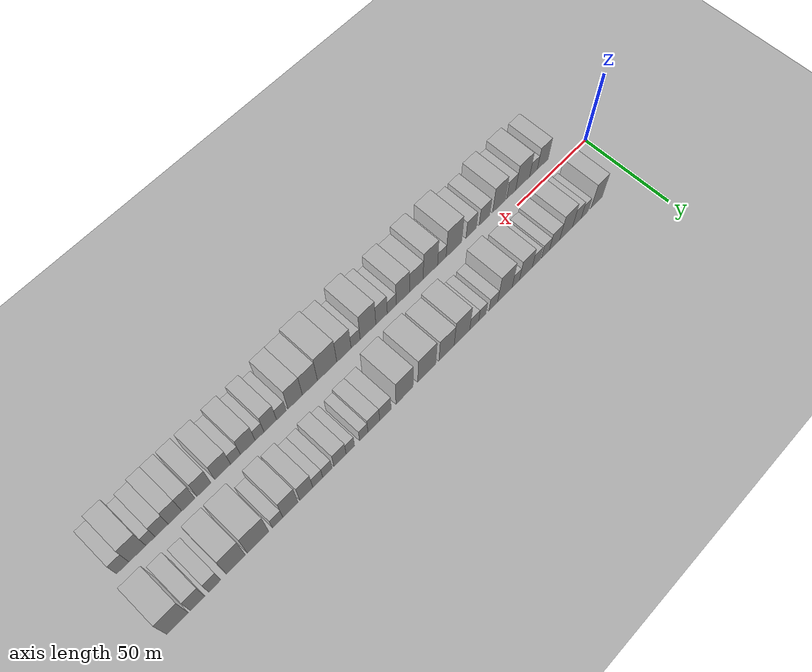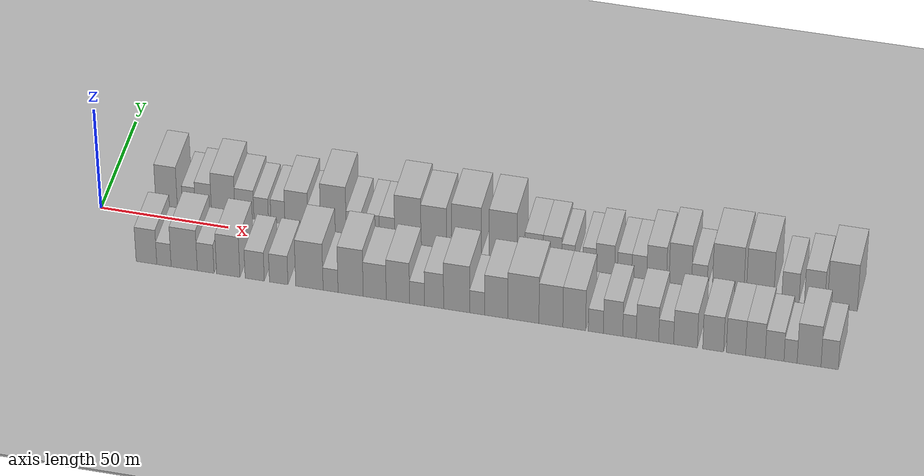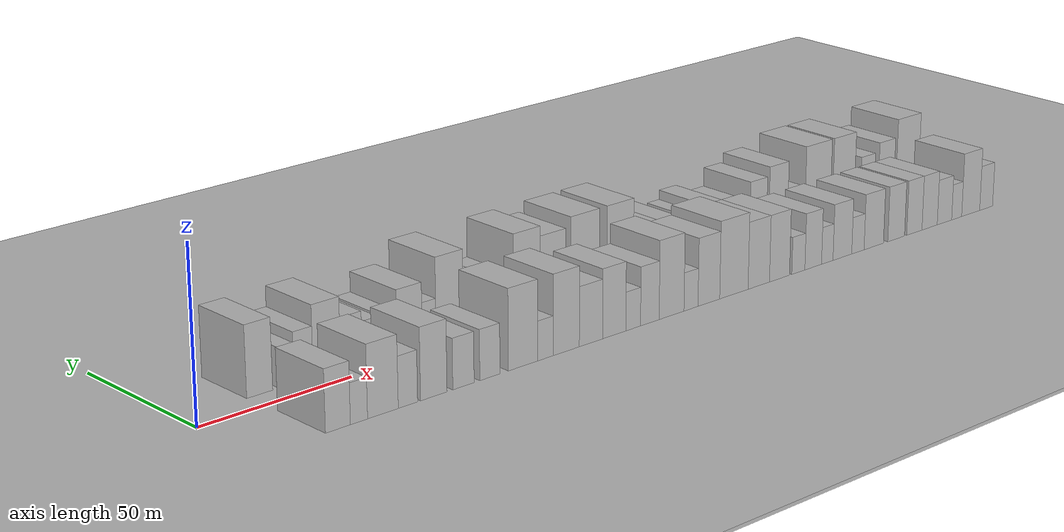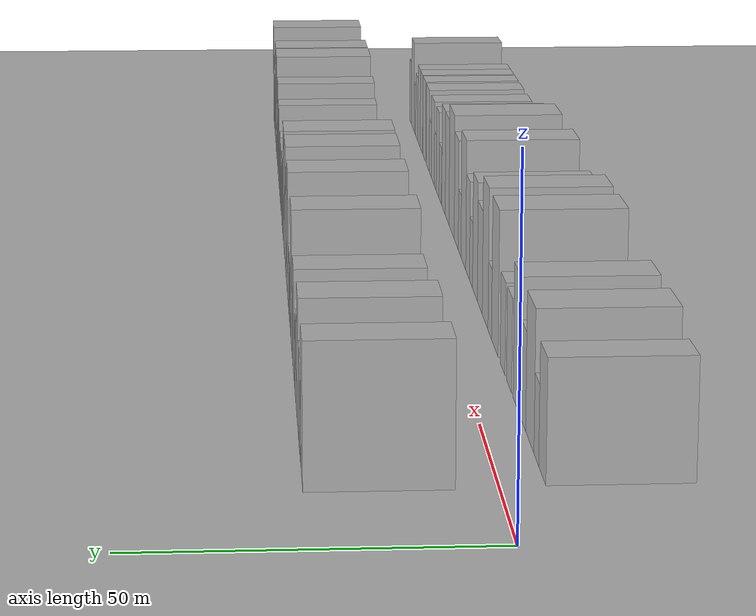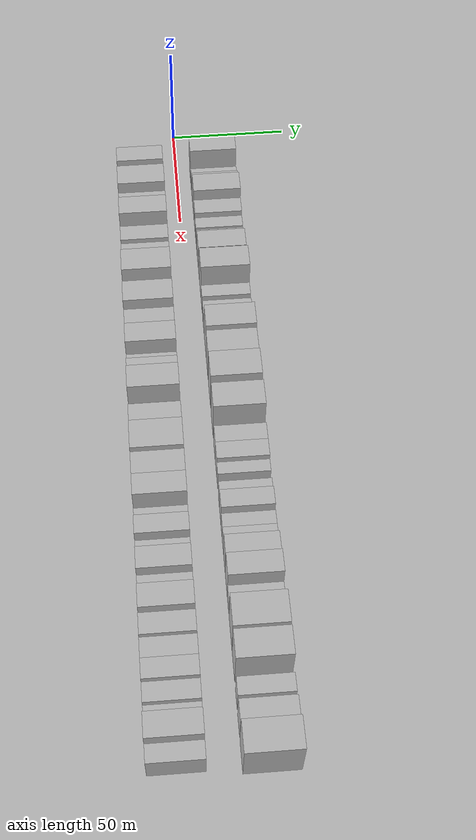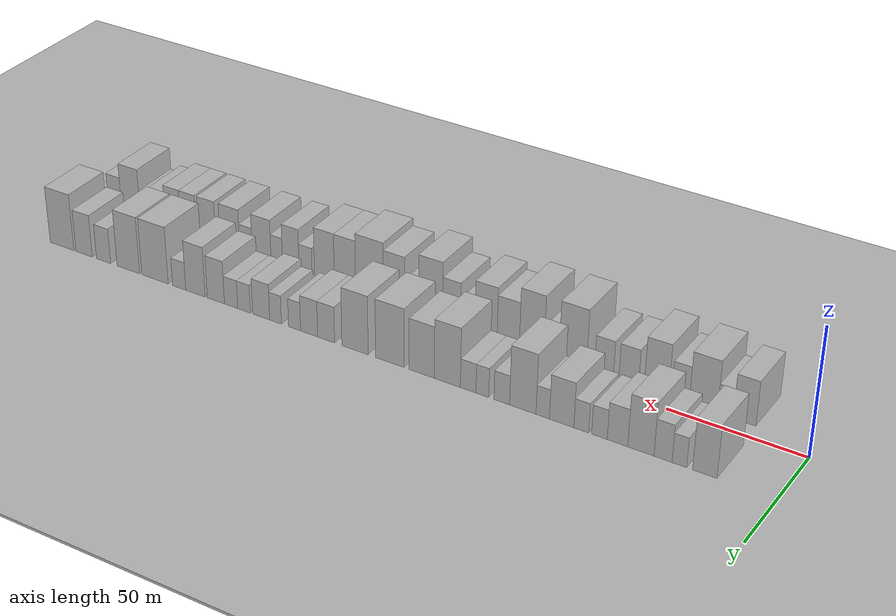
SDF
<?xml version="1.0" encoding="utf-8"?>

<sdf version="1.6">

   <world name="default">

      <gui fullscreen="0">

         <camera name="user_camera">

            <pose>-15 0 4.57585 0 0 0</pose>

            <view_controller>orbit</view_controller>

         </camera>

      </gui>

      <scene>

         <sky>

           <clouds>

             <speed>12</speed>

           </clouds>

         </sky>

         <ambient>0.4 0.4 0.4 1</ambient>

         <background>0.7 0.7 0.7 1</background>

         <shadows>1</shadows>

      </scene>

      <gravity>0 0 -9.8066</gravity>

      <magnetic_field>6e-06 2.3e-05 -4.2e-05</magnetic_field>

      <physics default="0" name="default_physics" type="ode">

         <ode>

            <solver>

               <type>quick</type>

               <iters>10</iters>

               <sor>1.0</sor>

               <use_dynamic_moi_rescaling>0</use_dynamic_moi_rescaling>

            </solver>

            <constraints>

               <cfm>0</cfm>

               <erp>0.2</erp>

               <contact_max_correcting_vel>100</contact_max_correcting_vel>

               <contact_surface_layer>0.001</contact_surface_layer>

            </constraints>

         </ode>

         <max_step_size>0.004</max_step_size>

         <real_time_factor>1</real_time_factor>

         <real_time_update_rate>250</real_time_update_rate>

      </physics>

      <light name="sun" type="directional">

         <cast_shadows>1</cast_shadows>

         <pose>0 0 10 0 0 0</pose>

         <diffuse>0.8 0.8 0.8 1</diffuse>

         <specular>0.2 0.2 0.2 1</specular>

         <attenuation>

            <range>1000</range>

            <constant>0.9</constant>

            <linear>0.01</linear>

            <quadratic>0.001</quadratic>

         </attenuation>

         <direction>-0.5 0.1 -0.9</direction>

      </light>

      <include>

         <name>ground_plane_1</name>

         <uri>model://HANNAS_ground_plane</uri>

         <pose>0 0 0  0 0 0</pose>

      </include>

      <include>

         <name>ground_plane_2</name>

         <uri>model://HANNAS_ground_plane</uri>

         <pose>100 0 0  0 0 0</pose>

      </include>

      <model name="building_1">

         <static>1</static>

         <pose frame="">24.2161 16.0000 0 0.000000 0.000000 1.570796</pose>

         <link name="link">

            <pose frame="">0 0 10.50 0 0 0</pose>

            <collision name="collision">

               <geometry>

                  <box>

                     <size>20.0000 8.4322 21.0000</size>

                  </box>

               </geometry>

               <max_contacts>10</max_contacts>

               <surface>

                  <contact>

                     <ode/>

                  </contact>

                  <bounce/>

                  <friction>

                     <torsional>

                        <ode/>

                     </torsional>

                     <ode/>

                  </friction>

               </surface>

            </collision>

            <visual name="visual">

               <cast_shadows>0</cast_shadows>

               <geometry>

                  <box>

                     <size>20.0000 8.4322 21.0000</size>

                  </box>

               </geometry>

               <material>

                  <script>

                     <uri>model://HANNAS_wall/materials/scripts</uri>

                     <uri>model://HANNAS_wall/materials/textures</uri>

                     <name>vrc/HANNAS_wall</name>

                  </script>

               </material>

            </visual>

            <self_collide>0</self_collide>

            <enable_wind>0</enable_wind>

            <kinematic>0</kinematic>

         </link>

      </model>

      <model name="building_2">

         <static>1</static>

         <pose frame="">32.9692 16.0000 0 0.000000 0.000000 1.570796</pose>

         <link name="link">

            <pose frame="">0 0 6.00 0 0 0</pose>

            <collision name="collision">

               <geometry>

                  <box>

                     <size>20.0000 5.0739 12.0000</size>

                  </box>

               </geometry>

               <max_contacts>10</max_contacts>

               <surface>

                  <contact>

                     <ode/>

                  </contact>

                  <bounce/>

                  <friction>

                     <torsional>

                        <ode/>

                     </torsional>

                     <ode/>

                  </friction>

               </surface>

            </collision>

            <visual name="visual">

               <cast_shadows>0</cast_shadows>

               <geometry>

                  <box>

                     <size>20.0000 5.0739 12.0000</size>

                  </box>

               </geometry>

               <material>

                  <script>

                     <uri>model://HANNAS_wall/materials/scripts</uri>

                     <uri>model://HANNAS_wall/materials/textures</uri>

                     <name>vrc/HANNAS_wall</name>

                  </script>

               </material>

            </visual>

            <self_collide>0</self_collide>

            <enable_wind>0</enable_wind>

            <kinematic>0</kinematic>

         </link>

      </model>

      <model name="building_3">

         <static>1</static>

         <pose frame="">38.6626 16.0000 0 0.000000 0.000000 1.570796</pose>

         <link name="link">

            <pose frame="">0 0 7.50 0 0 0</pose>

            <collision name="collision">

               <geometry>

                  <box>

                     <size>20.0000 6.3130 15.0000</size>

                  </box>

               </geometry>

               <max_contacts>10</max_contacts>

               <surface>

                  <contact>

                     <ode/>

                  </contact>

                  <bounce/>

                  <friction>

                     <torsional>

                        <ode/>

                     </torsional>

                     <ode/>

                  </friction>

               </surface>

            </collision>

            <visual name="visual">

               <cast_shadows>0</cast_shadows>

               <geometry>

                  <box>

                     <size>20.0000 6.3130 15.0000</size>

                  </box>

               </geometry>

               <material>

                  <script>

                     <uri>model://HANNAS_wall/materials/scripts</uri>

                     <uri>model://HANNAS_wall/materials/textures</uri>

                     <name>vrc/HANNAS_wall</name>

                  </script>

               </material>

            </visual>

            <self_collide>0</self_collide>

            <enable_wind>0</enable_wind>

            <kinematic>0</kinematic>

         </link>

      </model>

      <model name="building_4">

         <static>1</static>

         <pose frame="">46.4563 16.0000 0 0.000000 0.000000 1.570796</pose>

         <link name="link">

            <pose frame="">0 0 10.50 0 0 0</pose>

            <collision name="collision">

               <geometry>

                  <box>

                     <size>20.0000 9.2744 21.0000</size>

                  </box>

               </geometry>

               <max_contacts>10</max_contacts>

               <surface>

                  <contact>

                     <ode/>

                  </contact>

                  <bounce/>

                  <friction>

                     <torsional>

                        <ode/>

                     </torsional>

                     <ode/>

                  </friction>

               </surface>

            </collision>

            <visual name="visual">

               <cast_shadows>0</cast_shadows>

               <geometry>

                  <box>

                     <size>20.0000 9.2744 21.0000</size>

                  </box>

               </geometry>

               <material>

                  <script>

                     <uri>model://HANNAS_wall/materials/scripts</uri>

                     <uri>model://HANNAS_wall/materials/textures</uri>

                     <name>vrc/HANNAS_wall</name>

                  </script>

               </material>

            </visual>

            <self_collide>0</self_collide>

            <enable_wind>0</enable_wind>

            <kinematic>0</kinematic>

         </link>

      </model>

      <model name="building_5">

         <static>1</static>

         <pose frame="">54.7724 16.0000 0 0.000000 0.000000 1.570796</pose>

         <link name="link">

            <pose frame="">0 0 7.50 0 0 0</pose>

            <collision name="collision">

               <geometry>

                  <box>

                     <size>20.0000 7.3577 15.0000</size>

                  </box>

               </geometry>

               <max_contacts>10</max_contacts>

               <surface>

                  <contact>

                     <ode/>

                  </contact>

                  <bounce/>

                  <friction>

                     <torsional>

                        <ode/>

                     </torsional>

                     <ode/>

                  </friction>

               </surface>

            </collision>

            <visual name="visual">

               <cast_shadows>0</cast_shadows>

               <geometry>

                  <box>

                     <size>20.0000 7.3577 15.0000</size>

                  </box>

               </geometry>

               <material>

                  <script>

                     <uri>model://HANNAS_wall/materials/scripts</uri>

                     <uri>model://HANNAS_wall/materials/textures</uri>

                     <name>vrc/HANNAS_wall</name>

                  </script>

               </material>

            </visual>

            <self_collide>0</self_collide>

            <enable_wind>0</enable_wind>

            <kinematic>0</kinematic>

         </link>

      </model>

      <model name="building_6">

         <static>1</static>

         <pose frame="">61.2709 16.0000 0 0.000000 0.000000 1.570796</pose>

         <link name="link">

            <pose frame="">0 0 6.00 0 0 0</pose>

            <collision name="collision">

               <geometry>

                  <box>

                     <size>20.0000 5.6394 12.0000</size>

                  </box>

               </geometry>

               <max_contacts>10</max_contacts>

               <surface>

                  <contact>

                     <ode/>

                  </contact>

                  <bounce/>

                  <friction>

                     <torsional>

                        <ode/>

                     </torsional>

                     <ode/>

                  </friction>

               </surface>

            </collision>

            <visual name="visual">

               <cast_shadows>0</cast_shadows>

               <geometry>

                  <box>

                     <size>20.0000 5.6394 12.0000</size>

                  </box>

               </geometry>

               <material>

                  <script>

                     <uri>model://HANNAS_wall/materials/scripts</uri>

                     <uri>model://HANNAS_wall/materials/textures</uri>

                     <name>vrc/HANNAS_wall</name>

                  </script>

               </material>

            </visual>

            <self_collide>0</self_collide>

            <enable_wind>0</enable_wind>

            <kinematic>0</kinematic>

         </link>

      </model>

      <model name="building_7">

         <static>1</static>

         <pose frame="">67.8159 16.0000 0 0.000000 0.000000 1.570796</pose>

         <link name="link">

            <pose frame="">0 0 6.00 0 0 0</pose>

            <collision name="collision">

               <geometry>

                  <box>

                     <size>20.0000 5.4505 12.0000</size>

                  </box>

               </geometry>

               <max_contacts>10</max_contacts>

               <surface>

                  <contact>

                     <ode/>

                  </contact>

                  <bounce/>

                  <friction>

                     <torsional>

                        <ode/>

                     </torsional>

                     <ode/>

                  </friction>

               </surface>

            </collision>

            <visual name="visual">

               <cast_shadows>0</cast_shadows>

               <geometry>

                  <box>

                     <size>20.0000 5.4505 12.0000</size>

                  </box>

               </geometry>

               <material>

                  <script>

                     <uri>model://HANNAS_wall/materials/scripts</uri>

                     <uri>model://HANNAS_wall/materials/textures</uri>

                     <name>vrc/HANNAS_wall</name>

                  </script>

               </material>

            </visual>

            <self_collide>0</self_collide>

            <enable_wind>0</enable_wind>

            <kinematic>0</kinematic>

         </link>

      </model>

      <model name="building_8">

         <static>1</static>

         <pose frame="">75.0235 16.0000 0 0.000000 0.000000 1.570796</pose>

         <link name="link">

            <pose frame="">0 0 9.00 0 0 0</pose>

            <collision name="collision">

               <geometry>

                  <box>

                     <size>20.0000 8.9648 18.0000</size>

                  </box>

               </geometry>

               <max_contacts>10</max_contacts>

               <surface>

                  <contact>

                     <ode/>

                  </contact>

                  <bounce/>

                  <friction>

                     <torsional>

                        <ode/>

                     </torsional>

                     <ode/>

                  </friction>

               </surface>

            </collision>

            <visual name="visual">

               <cast_shadows>0</cast_shadows>

               <geometry>

                  <box>

                     <size>20.0000 8.9648 18.0000</size>

                  </box>

               </geometry>

               <material>

                  <script>

                     <uri>model://HANNAS_wall/materials/scripts</uri>

                     <uri>model://HANNAS_wall/materials/textures</uri>

                     <name>vrc/HANNAS_wall</name>

                  </script>

               </material>

            </visual>

            <self_collide>0</self_collide>

            <enable_wind>0</enable_wind>

            <kinematic>0</kinematic>

         </link>

      </model>

      <model name="building_9">

         <static>1</static>

         <pose frame="">82.0017 16.0000 0 0.000000 0.000000 1.570796</pose>

         <link name="link">

            <pose frame="">0 0 6.00 0 0 0</pose>

            <collision name="collision">

               <geometry>

                  <box>

                     <size>20.0000 4.9915 12.0000</size>

                  </box>

               </geometry>

               <max_contacts>10</max_contacts>

               <surface>

                  <contact>

                     <ode/>

                  </contact>

                  <bounce/>

                  <friction>

                     <torsional>

                        <ode/>

                     </torsional>

                     <ode/>

                  </friction>

               </surface>

            </collision>

            <visual name="visual">

               <cast_shadows>0</cast_shadows>

               <geometry>

                  <box>

                     <size>20.0000 4.9915 12.0000</size>

                  </box>

               </geometry>

               <material>

                  <script>

                     <uri>model://HANNAS_wall/materials/scripts</uri>

                     <uri>model://HANNAS_wall/materials/textures</uri>

                     <name>vrc/HANNAS_wall</name>

                  </script>

               </material>

            </visual>

            <self_collide>0</self_collide>

            <enable_wind>0</enable_wind>

            <kinematic>0</kinematic>

         </link>

      </model>

      <model name="building_10">

         <static>1</static>

         <pose frame="">89.4629 16.0000 0 0.000000 0.000000 1.570796</pose>

         <link name="link">

            <pose frame="">0 0 12.00 0 0 0</pose>

            <collision name="collision">

               <geometry>

                  <box>

                     <size>20.0000 9.9310 24.0000</size>

                  </box>

               </geometry>

               <max_contacts>10</max_contacts>

               <surface>

                  <contact>

                     <ode/>

                  </contact>

                  <bounce/>

                  <friction>

                     <torsional>

                        <ode/>

                     </torsional>

                     <ode/>

                  </friction>

               </surface>

            </collision>

            <visual name="visual">

               <cast_shadows>0</cast_shadows>

               <geometry>

                  <box>

                     <size>20.0000 9.9310 24.0000</size>

                  </box>

               </geometry>

               <material>

                  <script>

                     <uri>model://HANNAS_wall/materials/scripts</uri>

                     <uri>model://HANNAS_wall/materials/textures</uri>

                     <name>vrc/HANNAS_wall</name>

                  </script>

               </material>

            </visual>

            <self_collide>0</self_collide>

            <enable_wind>0</enable_wind>

            <kinematic>0</kinematic>

         </link>

      </model>

      <model name="building_11">

         <static>1</static>

         <pose frame="">97.3649 16.0000 0 0.000000 0.000000 1.570796</pose>

         <link name="link">

            <pose frame="">0 0 6.00 0 0 0</pose>

            <collision name="collision">

               <geometry>

                  <box>

                     <size>20.0000 5.8729 12.0000</size>

                  </box>

               </geometry>

               <max_contacts>10</max_contacts>

               <surface>

                  <contact>

                     <ode/>

                  </contact>

                  <bounce/>

                  <friction>

                     <torsional>

                        <ode/>

                     </torsional>

                     <ode/>

                  </friction>

               </surface>

            </collision>

            <visual name="visual">

               <cast_shadows>0</cast_shadows>

               <geometry>

                  <box>

                     <size>20.0000 5.8729 12.0000</size>

                  </box>

               </geometry>

               <material>

                  <script>

                     <uri>model://HANNAS_wall/materials/scripts</uri>

                     <uri>model://HANNAS_wall/materials/textures</uri>

                     <name>vrc/HANNAS_wall</name>

                  </script>

               </material>

            </visual>

            <self_collide>0</self_collide>

            <enable_wind>0</enable_wind>

            <kinematic>0</kinematic>

         </link>

      </model>

      <model name="building_12">

         <static>1</static>

         <pose frame="">104.7525 16.0000 0 0.000000 0.000000 1.570796</pose>

         <link name="link">

            <pose frame="">0 0 6.00 0 0 0</pose>

            <collision name="collision">

               <geometry>

                  <box>

                     <size>20.0000 4.9022 12.0000</size>

                  </box>

               </geometry>

               <max_contacts>10</max_contacts>

               <surface>

                  <contact>

                     <ode/>

                  </contact>

                  <bounce/>

                  <friction>

                     <torsional>

                        <ode/>

                     </torsional>

                     <ode/>

                  </friction>

               </surface>

            </collision>

            <visual name="visual">

               <cast_shadows>0</cast_shadows>

               <geometry>

                  <box>

                     <size>20.0000 4.9022 12.0000</size>

                  </box>

               </geometry>

               <material>

                  <script>

                     <uri>model://HANNAS_wall/materials/scripts</uri>

                     <uri>model://HANNAS_wall/materials/textures</uri>

                     <name>vrc/HANNAS_wall</name>

                  </script>

               </material>

            </visual>

            <self_collide>0</self_collide>

            <enable_wind>0</enable_wind>

            <kinematic>0</kinematic>

         </link>

      </model>

      <model name="building_13">

         <static>1</static>

         <pose frame="">110.1874 16.0000 0 0.000000 0.000000 1.570796</pose>

         <link name="link">

            <pose frame="">0 0 6.00 0 0 0</pose>

            <collision name="collision">

               <geometry>

                  <box>

                     <size>20.0000 5.9677 12.0000</size>

                  </box>

               </geometry>

               <max_contacts>10</max_contacts>

               <surface>

                  <contact>

                     <ode/>

                  </contact>

                  <bounce/>

                  <friction>

                     <torsional>

                        <ode/>

                     </torsional>

                     <ode/>

                  </friction>

               </surface>

            </collision>

            <visual name="visual">

               <cast_shadows>0</cast_shadows>

               <geometry>

                  <box>

                     <size>20.0000 5.9677 12.0000</size>

                  </box>

               </geometry>

               <material>

                  <script>

                     <uri>model://HANNAS_wall/materials/scripts</uri>

                     <uri>model://HANNAS_wall/materials/textures</uri>

                     <name>vrc/HANNAS_wall</name>

                  </script>

               </material>

            </visual>

            <self_collide>0</self_collide>

            <enable_wind>0</enable_wind>

            <kinematic>0</kinematic>

         </link>

      </model>

      <model name="building_14">

         <static>1</static>

         <pose frame="">118.2774 16.0000 0 0.000000 0.000000 1.570796</pose>

         <link name="link">

            <pose frame="">0 0 12.00 0 0 0</pose>

            <collision name="collision">

               <geometry>

                  <box>

                     <size>20.0000 10.2123 24.0000</size>

                  </box>

               </geometry>

               <max_contacts>10</max_contacts>

               <surface>

                  <contact>

                     <ode/>

                  </contact>

                  <bounce/>

                  <friction>

                     <torsional>

                        <ode/>

                     </torsional>

                     <ode/>

                  </friction>

               </surface>

            </collision>

            <visual name="visual">

               <cast_shadows>0</cast_shadows>

               <geometry>

                  <box>

                     <size>20.0000 10.2123 24.0000</size>

                  </box>

               </geometry>

               <material>

                  <script>

                     <uri>model://HANNAS_wall/materials/scripts</uri>

                     <uri>model://HANNAS_wall/materials/textures</uri>

                     <name>vrc/HANNAS_wall</name>

                  </script>

               </material>

            </visual>

            <self_collide>0</self_collide>

            <enable_wind>0</enable_wind>

            <kinematic>0</kinematic>

         </link>

      </model>

      <model name="building_15">

         <static>1</static>

         <pose frame="">128.3122 16.0000 0 0.000000 0.000000 1.570796</pose>

         <link name="link">

            <pose frame="">0 0 10.50 0 0 0</pose>

            <collision name="collision">

               <geometry>

                  <box>

                     <size>20.0000 9.8573 21.0000</size>

                  </box>

               </geometry>

               <max_contacts>10</max_contacts>

               <surface>

                  <contact>

                     <ode/>

                  </contact>

                  <bounce/>

                  <friction>

                     <torsional>

                        <ode/>

                     </torsional>

                     <ode/>

                  </friction>

               </surface>

            </collision>

            <visual name="visual">

               <cast_shadows>0</cast_shadows>

               <geometry>

                  <box>

                     <size>20.0000 9.8573 21.0000</size>

                  </box>

               </geometry>

               <material>

                  <script>

                     <uri>model://HANNAS_wall/materials/scripts</uri>

                     <uri>model://HANNAS_wall/materials/textures</uri>

                     <name>vrc/HANNAS_wall</name>

                  </script>

               </material>

            </visual>

            <self_collide>0</self_collide>

            <enable_wind>0</enable_wind>

            <kinematic>0</kinematic>

         </link>

      </model>

      <model name="building_16">

         <static>1</static>

         <pose frame="">140.9655 16.0000 0 0.000000 0.000000 1.570796</pose>

         <link name="link">

            <pose frame="">0 0 12.00 0 0 0</pose>

            <collision name="collision">

               <geometry>

                  <box>

                     <size>20.0000 11.4492 24.0000</size>

                  </box>

               </geometry>

               <max_contacts>10</max_contacts>

               <surface>

                  <contact>

                     <ode/>

                  </contact>

                  <bounce/>

                  <friction>

                     <torsional>

                        <ode/>

                     </torsional>

                     <ode/>

                  </friction>

               </surface>

            </collision>

            <visual name="visual">

               <cast_shadows>0</cast_shadows>

               <geometry>

                  <box>

                     <size>20.0000 11.4492 24.0000</size>

                  </box>

               </geometry>

               <material>

                  <script>

                     <uri>model://HANNAS_wall/materials/scripts</uri>

                     <uri>model://HANNAS_wall/materials/textures</uri>

                     <name>vrc/HANNAS_wall</name>

                  </script>

               </material>

            </visual>

            <self_collide>0</self_collide>

            <enable_wind>0</enable_wind>

            <kinematic>0</kinematic>

         </link>

      </model>

      <model name="building_17">

         <static>1</static>

         <pose frame="">155.0265 16.0000 0 0.000000 0.000000 1.570796</pose>

         <link name="link">

            <pose frame="">0 0 12.00 0 0 0</pose>

            <collision name="collision">

               <geometry>

                  <box>

                     <size>20.0000 10.6728 24.0000</size>

                  </box>

               </geometry>

               <max_contacts>10</max_contacts>

               <surface>

                  <contact>

                     <ode/>

                  </contact>

                  <bounce/>

                  <friction>

                     <torsional>

                        <ode/>

                     </torsional>

                     <ode/>

                  </friction>

               </surface>

            </collision>

            <visual name="visual">

               <cast_shadows>0</cast_shadows>

               <geometry>

                  <box>

                     <size>20.0000 10.6728 24.0000</size>

                  </box>

               </geometry>

               <material>

                  <script>

                     <uri>model://HANNAS_wall/materials/scripts</uri>

                     <uri>model://HANNAS_wall/materials/textures</uri>

                     <name>vrc/HANNAS_wall</name>

                  </script>

               </material>

            </visual>

            <self_collide>0</self_collide>

            <enable_wind>0</enable_wind>

            <kinematic>0</kinematic>

         </link>

      </model>

      <model name="building_18">

         <static>1</static>

         <pose frame="">166.8711 16.0000 0 0.000000 0.000000 1.570796</pose>

         <link name="link">

            <pose frame="">0 0 7.50 0 0 0</pose>

            <collision name="collision">

               <geometry>

                  <box>

                     <size>20.0000 7.0164 15.0000</size>

                  </box>

               </geometry>

               <max_contacts>10</max_contacts>

               <surface>

                  <contact>

                     <ode/>

                  </contact>

                  <bounce/>

                  <friction>

                     <torsional>

                        <ode/>

                     </torsional>

                     <ode/>

                  </friction>

               </surface>

            </collision>

            <visual name="visual">

               <cast_shadows>0</cast_shadows>

               <geometry>

                  <box>

                     <size>20.0000 7.0164 15.0000</size>

                  </box>

               </geometry>

               <material>

                  <script>

                     <uri>model://HANNAS_wall/materials/scripts</uri>

                     <uri>model://HANNAS_wall/materials/textures</uri>

                     <name>vrc/HANNAS_wall</name>

                  </script>

               </material>

            </visual>

            <self_collide>0</self_collide>

            <enable_wind>0</enable_wind>

            <kinematic>0</kinematic>

         </link>

      </model>

      <model name="building_19">

         <static>1</static>

         <pose frame="">173.9397 16.0000 0 0.000000 0.000000 1.570796</pose>

         <link name="link">

            <pose frame="">0 0 7.50 0 0 0</pose>

            <collision name="collision">

               <geometry>

                  <box>

                     <size>20.0000 7.1207 15.0000</size>

                  </box>

               </geometry>

               <max_contacts>10</max_contacts>

               <surface>

                  <contact>

                     <ode/>

                  </contact>

                  <bounce/>

                  <friction>

                     <torsional>

                        <ode/>

                     </torsional>

                     <ode/>

                  </friction>

               </surface>

            </collision>

            <visual name="visual">

               <cast_shadows>0</cast_shadows>

               <geometry>

                  <box>

                     <size>20.0000 7.1207 15.0000</size>

                  </box>

               </geometry>

               <material>

                  <script>

                     <uri>model://HANNAS_wall/materials/scripts</uri>

                     <uri>model://HANNAS_wall/materials/textures</uri>

                     <name>vrc/HANNAS_wall</name>

                  </script>

               </material>

            </visual>

            <self_collide>0</self_collide>

            <enable_wind>0</enable_wind>

            <kinematic>0</kinematic>

         </link>

      </model>

      <model name="building_20">

         <static>1</static>

         <pose frame="">180.0243 16.0000 0 0.000000 0.000000 1.570796</pose>

         <link name="link">

            <pose frame="">0 0 6.00 0 0 0</pose>

            <collision name="collision">

               <geometry>

                  <box>

                     <size>20.0000 5.0486 12.0000</size>

                  </box>

               </geometry>

               <max_contacts>10</max_contacts>

               <surface>

                  <contact>

                     <ode/>

                  </contact>

                  <bounce/>

                  <friction>

                     <torsional>

                        <ode/>

                     </torsional>

                     <ode/>

                  </friction>

               </surface>

            </collision>

            <visual name="visual">

               <cast_shadows>0</cast_shadows>

               <geometry>

                  <box>

                     <size>20.0000 5.0486 12.0000</size>

                  </box>

               </geometry>

               <material>

                  <script>

                     <uri>model://HANNAS_wall/materials/scripts</uri>

                     <uri>model://HANNAS_wall/materials/textures</uri>

                     <name>vrc/HANNAS_wall</name>

                  </script>

               </material>

            </visual>

            <self_collide>0</self_collide>

            <enable_wind>0</enable_wind>

            <kinematic>0</kinematic>

         </link>

      </model>

      <model name="building_21">

         <static>1</static>

         <pose frame="">188.0584 16.0000 0 0.000000 0.000000 1.570796</pose>

         <link name="link">

            <pose frame="">0 0 6.00 0 0 0</pose>

            <collision name="collision">

               <geometry>

                  <box>

                     <size>20.0000 5.0195 12.0000</size>

                  </box>

               </geometry>

               <max_contacts>10</max_contacts>

               <surface>

                  <contact>

                     <ode/>

                  </contact>

                  <bounce/>

                  <friction>

                     <torsional>

                        <ode/>

                     </torsional>

                     <ode/>

                  </friction>

               </surface>

            </collision>

            <visual name="visual">

               <cast_shadows>0</cast_shadows>

               <geometry>

                  <box>

                     <size>20.0000 5.0195 12.0000</size>

                  </box>

               </geometry>

               <material>

                  <script>

                     <uri>model://HANNAS_wall/materials/scripts</uri>

                     <uri>model://HANNAS_wall/materials/textures</uri>

                     <name>vrc/HANNAS_wall</name>

                  </script>

               </material>

            </visual>

            <self_collide>0</self_collide>

            <enable_wind>0</enable_wind>

            <kinematic>0</kinematic>

         </link>

      </model>

      <model name="building_22">

         <static>1</static>

         <pose frame="">194.2041 16.0000 0 0.000000 0.000000 1.570796</pose>

         <link name="link">

            <pose frame="">0 0 7.50 0 0 0</pose>

            <collision name="collision">

               <geometry>

                  <box>

                     <size>20.0000 7.2721 15.0000</size>

                  </box>

               </geometry>

               <max_contacts>10</max_contacts>

               <surface>

                  <contact>

                     <ode/>

                  </contact>

                  <bounce/>

                  <friction>

                     <torsional>

                        <ode/>

                     </torsional>

                     <ode/>

                  </friction>

               </surface>

            </collision>

            <visual name="visual">

               <cast_shadows>0</cast_shadows>

               <geometry>

                  <box>

                     <size>20.0000 7.2721 15.0000</size>

                  </box>

               </geometry>

               <material>

                  <script>

                     <uri>model://HANNAS_wall/materials/scripts</uri>

                     <uri>model://HANNAS_wall/materials/textures</uri>

                     <name>vrc/HANNAS_wall</name>

                  </script>

               </material>

            </visual>

            <self_collide>0</self_collide>

            <enable_wind>0</enable_wind>

            <kinematic>0</kinematic>

         </link>

      </model>

      <model name="building_23">

         <static>1</static>

         <pose frame="">201.5783 16.0000 0 0.000000 0.000000 1.570796</pose>

         <link name="link">

            <pose frame="">0 0 6.00 0 0 0</pose>

            <collision name="collision">

               <geometry>

                  <box>

                     <size>20.0000 5.4761 12.0000</size>

                  </box>

               </geometry>

               <max_contacts>10</max_contacts>

               <surface>

                  <contact>

                     <ode/>

                  </contact>

                  <bounce/>

                  <friction>

                     <torsional>

                        <ode/>

                     </torsional>

                     <ode/>

                  </friction>

               </surface>

            </collision>

            <visual name="visual">

               <cast_shadows>0</cast_shadows>

               <geometry>

                  <box>

                     <size>20.0000 5.4761 12.0000</size>

                  </box>

               </geometry>

               <material>

                  <script>

                     <uri>model://HANNAS_wall/materials/scripts</uri>

                     <uri>model://HANNAS_wall/materials/textures</uri>

                     <name>vrc/HANNAS_wall</name>

                  </script>

               </material>

            </visual>

            <self_collide>0</self_collide>

            <enable_wind>0</enable_wind>

            <kinematic>0</kinematic>

         </link>

      </model>

      <model name="building_24">

         <static>1</static>

         <pose frame="">207.1888 16.0000 0 0.000000 0.000000 1.570796</pose>

         <link name="link">

            <pose frame="">0 0 6.00 0 0 0</pose>

            <collision name="collision">

               <geometry>

                  <box>

                     <size>20.0000 5.7449 12.0000</size>

                  </box>

               </geometry>

               <max_contacts>10</max_contacts>

               <surface>

                  <contact>

                     <ode/>

                  </contact>

                  <bounce/>

                  <friction>

                     <torsional>

                        <ode/>

                     </torsional>

                     <ode/>

                  </friction>

               </surface>

            </collision>

            <visual name="visual">

               <cast_shadows>0</cast_shadows>

               <geometry>

                  <box>

                     <size>20.0000 5.7449 12.0000</size>

                  </box>

               </geometry>

               <material>

                  <script>

                     <uri>model://HANNAS_wall/materials/scripts</uri>

                     <uri>model://HANNAS_wall/materials/textures</uri>

                     <name>vrc/HANNAS_wall</name>

                  </script>

               </material>

            </visual>

            <self_collide>0</self_collide>

            <enable_wind>0</enable_wind>

            <kinematic>0</kinematic>

         </link>

      </model>

      <model name="building_25">

         <static>1</static>

         <pose frame="">213.8096 16.0000 0 0.000000 0.000000 1.570796</pose>

         <link name="link">

            <pose frame="">0 0 9.00 0 0 0</pose>

            <collision name="collision">

               <geometry>

                  <box>

                     <size>20.0000 7.4967 18.0000</size>

                  </box>

               </geometry>

               <max_contacts>10</max_contacts>

               <surface>

                  <contact>

                     <ode/>

                  </contact>

                  <bounce/>

                  <friction>

                     <torsional>

                        <ode/>

                     </torsional>

                     <ode/>

                  </friction>

               </surface>

            </collision>

            <visual name="visual">

               <cast_shadows>0</cast_shadows>

               <geometry>

                  <box>

                     <size>20.0000 7.4967 18.0000</size>

                  </box>

               </geometry>

               <material>

                  <script>

                     <uri>model://HANNAS_wall/materials/scripts</uri>

                     <uri>model://HANNAS_wall/materials/textures</uri>

                     <name>vrc/HANNAS_wall</name>

                  </script>

               </material>

            </visual>

            <self_collide>0</self_collide>

            <enable_wind>0</enable_wind>

            <kinematic>0</kinematic>

         </link>

      </model>

      <model name="building_26">

         <static>1</static>

         <pose frame="">222.8315 16.0000 0 0.000000 0.000000 1.570796</pose>

         <link name="link">

            <pose frame="">0 0 10.50 0 0 0</pose>

            <collision name="collision">

               <geometry>

                  <box>

                     <size>20.0000 8.5472 21.0000</size>

                  </box>

               </geometry>

               <max_contacts>10</max_contacts>

               <surface>

                  <contact>

                     <ode/>

                  </contact>

                  <bounce/>

                  <friction>

                     <torsional>

                        <ode/>

                     </torsional>

                     <ode/>

                  </friction>

               </surface>

            </collision>

            <visual name="visual">

               <cast_shadows>0</cast_shadows>

               <geometry>

                  <box>

                     <size>20.0000 8.5472 21.0000</size>

                  </box>

               </geometry>

               <material>

                  <script>

                     <uri>model://HANNAS_wall/materials/scripts</uri>

                     <uri>model://HANNAS_wall/materials/textures</uri>

                     <name>vrc/HANNAS_wall</name>

                  </script>

               </material>

            </visual>

            <self_collide>0</self_collide>

            <enable_wind>0</enable_wind>

            <kinematic>0</kinematic>

         </link>

      </model>

      <model name="building_27">

         <static>1</static>

         <pose frame="">230.0566 16.0000 0 0.000000 0.000000 1.570796</pose>

         <link name="link">

            <pose frame="">0 0 6.00 0 0 0</pose>

            <collision name="collision">

               <geometry>

                  <box>

                     <size>20.0000 5.9030 12.0000</size>

                  </box>

               </geometry>

               <max_contacts>10</max_contacts>

               <surface>

                  <contact>

                     <ode/>

                  </contact>

                  <bounce/>

                  <friction>

                     <torsional>

                        <ode/>

                     </torsional>

                     <ode/>

                  </friction>

               </surface>

            </collision>

            <visual name="visual">

               <cast_shadows>0</cast_shadows>

               <geometry>

                  <box>

                     <size>20.0000 5.9030 12.0000</size>

                  </box>

               </geometry>

               <material>

                  <script>

                     <uri>model://HANNAS_wall/materials/scripts</uri>

                     <uri>model://HANNAS_wall/materials/textures</uri>

                     <name>vrc/HANNAS_wall</name>

                  </script>

               </material>

            </visual>

            <self_collide>0</self_collide>

            <enable_wind>0</enable_wind>

            <kinematic>0</kinematic>

         </link>

      </model>

      <model name="building_28">

         <static>1</static>

         <pose frame="">240.9556 16.0000 0 0.000000 0.000000 1.570796</pose>

         <link name="link">

            <pose frame="">0 0 12.00 0 0 0</pose>

            <collision name="collision">

               <geometry>

                  <box>

                     <size>20.0000 11.8950 24.0000</size>

                  </box>

               </geometry>

               <max_contacts>10</max_contacts>

               <surface>

                  <contact>

                     <ode/>

                  </contact>

                  <bounce/>

                  <friction>

                     <torsional>

                        <ode/>

                     </torsional>

                     <ode/>

                  </friction>

               </surface>

            </collision>

            <visual name="visual">

               <cast_shadows>0</cast_shadows>

               <geometry>

                  <box>

                     <size>20.0000 11.8950 24.0000</size>

                  </box>

               </geometry>

               <material>

                  <script>

                     <uri>model://HANNAS_wall/materials/scripts</uri>

                     <uri>model://HANNAS_wall/materials/textures</uri>

                     <name>vrc/HANNAS_wall</name>

                  </script>

               </material>

            </visual>

            <self_collide>0</self_collide>

            <enable_wind>0</enable_wind>

            <kinematic>0</kinematic>

         </link>

      </model>

      <model name="building_29">

         <static>1</static>

         <pose frame="">253.0894 16.0000 0 0.000000 0.000000 1.570796</pose>

         <link name="link">

            <pose frame="">0 0 12.00 0 0 0</pose>

            <collision name="collision">

               <geometry>

                  <box>

                     <size>20.0000 10.3726 24.0000</size>

                  </box>

               </geometry>

               <max_contacts>10</max_contacts>

               <surface>

                  <contact>

                     <ode/>

                  </contact>

                  <bounce/>

                  <friction>

                     <torsional>

                        <ode/>

                     </torsional>

                     <ode/>

                  </friction>

               </surface>

            </collision>

            <visual name="visual">

               <cast_shadows>0</cast_shadows>

               <geometry>

                  <box>

                     <size>20.0000 10.3726 24.0000</size>

                  </box>

               </geometry>

               <material>

                  <script>

                     <uri>model://HANNAS_wall/materials/scripts</uri>

                     <uri>model://HANNAS_wall/materials/textures</uri>

                     <name>vrc/HANNAS_wall</name>

                  </script>

               </material>

            </visual>

            <self_collide>0</self_collide>

            <enable_wind>0</enable_wind>

            <kinematic>0</kinematic>

         </link>

      </model>

      <model name="building_30">

         <static>1</static>

         <pose frame="">264.5663 16.0000 0 0.000000 0.000000 1.570796</pose>

         <link name="link">

            <pose frame="">0 0 7.50 0 0 0</pose>

            <collision name="collision">

               <geometry>

                  <box>

                     <size>20.0000 6.5811 15.0000</size>

                  </box>

               </geometry>

               <max_contacts>10</max_contacts>

               <surface>

                  <contact>

                     <ode/>

                  </contact>

                  <bounce/>

                  <friction>

                     <torsional>

                        <ode/>

                     </torsional>

                     <ode/>

                  </friction>

               </surface>

            </collision>

            <visual name="visual">

               <cast_shadows>0</cast_shadows>

               <geometry>

                  <box>

                     <size>20.0000 6.5811 15.0000</size>

                  </box>

               </geometry>

               <material>

                  <script>

                     <uri>model://HANNAS_wall/materials/scripts</uri>

                     <uri>model://HANNAS_wall/materials/textures</uri>

                     <name>vrc/HANNAS_wall</name>

                  </script>

               </material>

            </visual>

            <self_collide>0</self_collide>

            <enable_wind>0</enable_wind>

            <kinematic>0</kinematic>

         </link>

      </model>

      <model name="building_31">

         <static>1</static>

         <pose frame="">273.6921 16.0000 0 0.000000 0.000000 1.570796</pose>

         <link name="link">

            <pose frame="">0 0 9.00 0 0 0</pose>

            <collision name="collision">

               <geometry>

                  <box>

                     <size>20.0000 7.6704 18.0000</size>

                  </box>

               </geometry>

               <max_contacts>10</max_contacts>

               <surface>

                  <contact>

                     <ode/>

                  </contact>

                  <bounce/>

                  <friction>

                     <torsional>

                        <ode/>

                     </torsional>

                     <ode/>

                  </friction>

               </surface>

            </collision>

            <visual name="visual">

               <cast_shadows>0</cast_shadows>

               <geometry>

                  <box>

                     <size>20.0000 7.6704 18.0000</size>

                  </box>

               </geometry>

               <material>

                  <script>

                     <uri>model://HANNAS_wall/materials/scripts</uri>

                     <uri>model://HANNAS_wall/materials/textures</uri>

                     <name>vrc/HANNAS_wall</name>

                  </script>

               </material>

            </visual>

            <self_collide>0</self_collide>

            <enable_wind>0</enable_wind>

            <kinematic>0</kinematic>

         </link>

      </model>

      <model name="building_32">

         <static>1</static>

         <pose frame="">284.1521 16.0000 0 0.000000 0.000000 1.570796</pose>

         <link name="link">

            <pose frame="">0 0 12.00 0 0 0</pose>

            <collision name="collision">

               <geometry>

                  <box>

                     <size>20.0000 11.2497 24.0000</size>

                  </box>

               </geometry>

               <max_contacts>10</max_contacts>

               <surface>

                  <contact>

                     <ode/>

                  </contact>

                  <bounce/>

                  <friction>

                     <torsional>

                        <ode/>

                     </torsional>

                     <ode/>

                  </friction>

               </surface>

            </collision>

            <visual name="visual">

               <cast_shadows>0</cast_shadows>

               <geometry>

                  <box>

                     <size>20.0000 11.2497 24.0000</size>

                  </box>

               </geometry>

               <material>

                  <script>

                     <uri>model://HANNAS_wall/materials/scripts</uri>

                     <uri>model://HANNAS_wall/materials/textures</uri>

                     <name>vrc/HANNAS_wall</name>

                  </script>

               </material>

            </visual>

            <self_collide>0</self_collide>

            <enable_wind>0</enable_wind>

            <kinematic>0</kinematic>

         </link>

      </model>

      <model name="building_33">

         <static>1</static>

         <pose frame="">25.0130 -16.0000 0 0.000000 0.000000 1.570796</pose>

         <link name="link">

            <pose frame="">0 0 9.00 0 0 0</pose>

            <collision name="collision">

               <geometry>

                  <box>

                     <size>20.0000 8.0260 18.0000</size>

                  </box>

               </geometry>

               <max_contacts>10</max_contacts>

               <surface>

                  <contact>

                     <ode/>

                  </contact>

                  <bounce/>

                  <friction>

                     <torsional>

                        <ode/>

                     </torsional>

                     <ode/>

                  </friction>

               </surface>

            </collision>

            <visual name="visual">

               <cast_shadows>0</cast_shadows>

               <geometry>

                  <box>

                     <size>20.0000 8.0260 18.0000</size>

                  </box>

               </geometry>

               <material>

                  <script>

                     <uri>model://HANNAS_wall/materials/scripts</uri>

                     <uri>model://HANNAS_wall/materials/textures</uri>

                     <name>vrc/HANNAS_wall</name>

                  </script>

               </material>

            </visual>

            <self_collide>0</self_collide>

            <enable_wind>0</enable_wind>

            <kinematic>0</kinematic>

         </link>

      </model>

      <model name="building_34">

         <static>1</static>

         <pose frame="">31.8116 -16.0000 0 0.000000 0.000000 1.570796</pose>

         <link name="link">

            <pose frame="">0 0 6.00 0 0 0</pose>

            <collision name="collision">

               <geometry>

                  <box>

                     <size>20.0000 5.5711 12.0000</size>

                  </box>

               </geometry>

               <max_contacts>10</max_contacts>

               <surface>

                  <contact>

                     <ode/>

                  </contact>

                  <bounce/>

                  <friction>

                     <torsional>

                        <ode/>

                     </torsional>

                     <ode/>

                  </friction>

               </surface>

            </collision>

            <visual name="visual">

               <cast_shadows>0</cast_shadows>

               <geometry>

                  <box>

                     <size>20.0000 5.5711 12.0000</size>

                  </box>

               </geometry>

               <material>

                  <script>

                     <uri>model://HANNAS_wall/materials/scripts</uri>

                     <uri>model://HANNAS_wall/materials/textures</uri>

                     <name>vrc/HANNAS_wall</name>

                  </script>

               </material>

            </visual>

            <self_collide>0</self_collide>

            <enable_wind>0</enable_wind>

            <kinematic>0</kinematic>

         </link>

      </model>

      <model name="building_35">

         <static>1</static>

         <pose frame="">39.6670 -16.0000 0 0.000000 0.000000 1.570796</pose>

         <link name="link">

            <pose frame="">0 0 10.50 0 0 0</pose>

            <collision name="collision">

               <geometry>

                  <box>

                     <size>20.0000 10.1397 21.0000</size>

                  </box>

               </geometry>

               <max_contacts>10</max_contacts>

               <surface>

                  <contact>

                     <ode/>

                  </contact>

                  <bounce/>

                  <friction>

                     <torsional>

                        <ode/>

                     </torsional>

                     <ode/>

                  </friction>

               </surface>

            </collision>

            <visual name="visual">

               <cast_shadows>0</cast_shadows>

               <geometry>

                  <box>

                     <size>20.0000 10.1397 21.0000</size>

                  </box>

               </geometry>

               <material>

                  <script>

                     <uri>model://HANNAS_wall/materials/scripts</uri>

                     <uri>model://HANNAS_wall/materials/textures</uri>

                     <name>vrc/HANNAS_wall</name>

                  </script>

               </material>

            </visual>

            <self_collide>0</self_collide>

            <enable_wind>0</enable_wind>

            <kinematic>0</kinematic>

         </link>

      </model>

      <model name="building_36">

         <static>1</static>

         <pose frame="">47.9755 -16.0000 0 0.000000 0.000000 1.570796</pose>

         <link name="link">

            <pose frame="">0 0 7.50 0 0 0</pose>

            <collision name="collision">

               <geometry>

                  <box>

                     <size>20.0000 6.4773 15.0000</size>

                  </box>

               </geometry>

               <max_contacts>10</max_contacts>

               <surface>

                  <contact>

                     <ode/>

                  </contact>

                  <bounce/>

                  <friction>

                     <torsional>

                        <ode/>

                     </torsional>

                     <ode/>

                  </friction>

               </surface>

            </collision>

            <visual name="visual">

               <cast_shadows>0</cast_shadows>

               <geometry>

                  <box>

                     <size>20.0000 6.4773 15.0000</size>

                  </box>

               </geometry>

               <material>

                  <script>

                     <uri>model://HANNAS_wall/materials/scripts</uri>

                     <uri>model://HANNAS_wall/materials/textures</uri>

                     <name>vrc/HANNAS_wall</name>

                  </script>

               </material>

            </visual>

            <self_collide>0</self_collide>

            <enable_wind>0</enable_wind>

            <kinematic>0</kinematic>

         </link>

      </model>

      <model name="building_37">

         <static>1</static>

         <pose frame="">56.7208 -16.0000 0 0.000000 0.000000 1.570796</pose>

         <link name="link">

            <pose frame="">0 0 10.50 0 0 0</pose>

            <collision name="collision">

               <geometry>

                  <box>

                     <size>20.0000 9.0133 21.0000</size>

                  </box>

               </geometry>

               <max_contacts>10</max_contacts>

               <surface>

                  <contact>

                     <ode/>

                  </contact>

                  <bounce/>

                  <friction>

                     <torsional>

                        <ode/>

                     </torsional>

                     <ode/>

                  </friction>

               </surface>

            </collision>

            <visual name="visual">

               <cast_shadows>0</cast_shadows>

               <geometry>

                  <box>

                     <size>20.0000 9.0133 21.0000</size>

                  </box>

               </geometry>

               <material>

                  <script>

                     <uri>model://HANNAS_wall/materials/scripts</uri>

                     <uri>model://HANNAS_wall/materials/textures</uri>

                     <name>vrc/HANNAS_wall</name>

                  </script>

               </material>

            </visual>

            <self_collide>0</self_collide>

            <enable_wind>0</enable_wind>

            <kinematic>0</kinematic>

         </link>

      </model>

      <model name="building_38">

         <static>1</static>

         <pose frame="">66.9238 -16.0000 0 0.000000 0.000000 1.570796</pose>

         <link name="link">

            <pose frame="">0 0 7.50 0 0 0</pose>

            <collision name="collision">

               <geometry>

                  <box>

                     <size>20.0000 7.3926 15.0000</size>

                  </box>

               </geometry>

               <max_contacts>10</max_contacts>

               <surface>

                  <contact>

                     <ode/>

                  </contact>

                  <bounce/>

                  <friction>

                     <torsional>

                        <ode/>

                     </torsional>

                     <ode/>

                  </friction>

               </surface>

            </collision>

            <visual name="visual">

               <cast_shadows>0</cast_shadows>

               <geometry>

                  <box>

                     <size>20.0000 7.3926 15.0000</size>

                  </box>

               </geometry>

               <material>

                  <script>

                     <uri>model://HANNAS_wall/materials/scripts</uri>

                     <uri>model://HANNAS_wall/materials/textures</uri>

                     <name>vrc/HANNAS_wall</name>

                  </script>

               </material>

            </visual>

            <self_collide>0</self_collide>

            <enable_wind>0</enable_wind>

            <kinematic>0</kinematic>

         </link>

      </model>

      <model name="building_39">

         <static>1</static>

         <pose frame="">76.1817 -16.0000 0 0.000000 0.000000 1.570796</pose>

         <link name="link">

            <pose frame="">0 0 7.50 0 0 0</pose>

            <collision name="collision">

               <geometry>

                  <box>

                     <size>20.0000 7.1232 15.0000</size>

                  </box>

               </geometry>

               <max_contacts>10</max_contacts>

               <surface>

                  <contact>

                     <ode/>

                  </contact>

                  <bounce/>

                  <friction>

                     <torsional>

                        <ode/>

                     </torsional>

                     <ode/>

                  </friction>

               </surface>

            </collision>

            <visual name="visual">

               <cast_shadows>0</cast_shadows>

               <geometry>

                  <box>

                     <size>20.0000 7.1232 15.0000</size>

                  </box>

               </geometry>

               <material>

                  <script>

                     <uri>model://HANNAS_wall/materials/scripts</uri>

                     <uri>model://HANNAS_wall/materials/textures</uri>

                     <name>vrc/HANNAS_wall</name>

                  </script>

               </material>

            </visual>

            <self_collide>0</self_collide>

            <enable_wind>0</enable_wind>

            <kinematic>0</kinematic>

         </link>

      </model>

      <model name="building_40">

         <static>1</static>

         <pose frame="">88.0166 -16.0000 0 0.000000 0.000000 1.570796</pose>

         <link name="link">

            <pose frame="">0 0 12.00 0 0 0</pose>

            <collision name="collision">

               <geometry>

                  <box>

                     <size>20.0000 10.5466 24.0000</size>

                  </box>

               </geometry>

               <max_contacts>10</max_contacts>

               <surface>

                  <contact>

                     <ode/>

                  </contact>

                  <bounce/>

                  <friction>

                     <torsional>

                        <ode/>

                     </torsional>

                     <ode/>

                  </friction>

               </surface>

            </collision>

            <visual name="visual">

               <cast_shadows>0</cast_shadows>

               <geometry>

                  <box>

                     <size>20.0000 10.5466 24.0000</size>

                  </box>

               </geometry>

               <material>

                  <script>

                     <uri>model://HANNAS_wall/materials/scripts</uri>

                     <uri>model://HANNAS_wall/materials/textures</uri>

                     <name>vrc/HANNAS_wall</name>

                  </script>

               </material>

            </visual>

            <self_collide>0</self_collide>

            <enable_wind>0</enable_wind>

            <kinematic>0</kinematic>

         </link>

      </model>

      <model name="building_41">

         <static>1</static>

         <pose frame="">96.1535 -16.0000 0 0.000000 0.000000 1.570796</pose>

         <link name="link">

            <pose frame="">0 0 6.00 0 0 0</pose>

            <collision name="collision">

               <geometry>

                  <box>

                     <size>20.0000 5.7273 12.0000</size>

                  </box>

               </geometry>

               <max_contacts>10</max_contacts>

               <surface>

                  <contact>

                     <ode/>

                  </contact>

                  <bounce/>

                  <friction>

                     <torsional>

                        <ode/>

                     </torsional>

                     <ode/>

                  </friction>

               </surface>

            </collision>

            <visual name="visual">

               <cast_shadows>0</cast_shadows>

               <geometry>

                  <box>

                     <size>20.0000 5.7273 12.0000</size>

                  </box>

               </geometry>

               <material>

                  <script>

                     <uri>model://HANNAS_wall/materials/scripts</uri>

                     <uri>model://HANNAS_wall/materials/textures</uri>

                     <name>vrc/HANNAS_wall</name>

                  </script>

               </material>

            </visual>

            <self_collide>0</self_collide>

            <enable_wind>0</enable_wind>

            <kinematic>0</kinematic>

         </link>

      </model>

      <model name="building_42">

         <static>1</static>

         <pose frame="">103.8464 -16.0000 0 0.000000 0.000000 1.570796</pose>

         <link name="link">

            <pose frame="">0 0 12.00 0 0 0</pose>

            <collision name="collision">

               <geometry>

                  <box>

                     <size>20.0000 9.6585 24.0000</size>

                  </box>

               </geometry>

               <max_contacts>10</max_contacts>

               <surface>

                  <contact>

                     <ode/>

                  </contact>

                  <bounce/>

                  <friction>

                     <torsional>

                        <ode/>

                     </torsional>

                     <ode/>

                  </friction>

               </surface>

            </collision>

            <visual name="visual">

               <cast_shadows>0</cast_shadows>

               <geometry>

                  <box>

                     <size>20.0000 9.6585 24.0000</size>

                  </box>

               </geometry>

               <material>

                  <script>

                     <uri>model://HANNAS_wall/materials/scripts</uri>

                     <uri>model://HANNAS_wall/materials/textures</uri>

                     <name>vrc/HANNAS_wall</name>

                  </script>

               </material>

            </visual>

            <self_collide>0</self_collide>

            <enable_wind>0</enable_wind>

            <kinematic>0</kinematic>

         </link>

      </model>

      <model name="building_43">

         <static>1</static>

         <pose frame="">113.0781 -16.0000 0 0.000000 0.000000 1.570796</pose>

         <link name="link">

            <pose frame="">0 0 9.00 0 0 0</pose>

            <collision name="collision">

               <geometry>

                  <box>

                     <size>20.0000 8.8050 18.0000</size>

                  </box>

               </geometry>

               <max_contacts>10</max_contacts>

               <surface>

                  <contact>

                     <ode/>

                  </contact>

                  <bounce/>

                  <friction>

                     <torsional>

                        <ode/>

                     </torsional>

                     <ode/>

                  </friction>

               </surface>

            </collision>

            <visual name="visual">

               <cast_shadows>0</cast_shadows>

               <geometry>

                  <box>

                     <size>20.0000 8.8050 18.0000</size>

                  </box>

               </geometry>

               <material>

                  <script>

                     <uri>model://HANNAS_wall/materials/scripts</uri>

                     <uri>model://HANNAS_wall/materials/textures</uri>

                     <name>vrc/HANNAS_wall</name>

                  </script>

               </material>

            </visual>

            <self_collide>0</self_collide>

            <enable_wind>0</enable_wind>

            <kinematic>0</kinematic>

         </link>

      </model>

      <model name="building_44">

         <static>1</static>

         <pose frame="">121.9330 -16.0000 0 0.000000 0.000000 1.570796</pose>

         <link name="link">

            <pose frame="">0 0 10.50 0 0 0</pose>

            <collision name="collision">

               <geometry>

                  <box>

                     <size>20.0000 8.9048 21.0000</size>

                  </box>

               </geometry>

               <max_contacts>10</max_contacts>

               <surface>

                  <contact>

                     <ode/>

                  </contact>

                  <bounce/>

                  <friction>

                     <torsional>

                        <ode/>

                     </torsional>

                     <ode/>

                  </friction>

               </surface>

            </collision>

            <visual name="visual">

               <cast_shadows>0</cast_shadows>

               <geometry>

                  <box>

                     <size>20.0000 8.9048 21.0000</size>

                  </box>

               </geometry>

               <material>

                  <script>

                     <uri>model://HANNAS_wall/materials/scripts</uri>

                     <uri>model://HANNAS_wall/materials/textures</uri>

                     <name>vrc/HANNAS_wall</name>

                  </script>

               </material>

            </visual>

            <self_collide>0</self_collide>

            <enable_wind>0</enable_wind>

            <kinematic>0</kinematic>

         </link>

      </model>

      <model name="building_45">

         <static>1</static>

         <pose frame="">129.2344 -16.0000 0 0.000000 0.000000 1.570796</pose>

         <link name="link">

            <pose frame="">0 0 6.00 0 0 0</pose>

            <collision name="collision">

               <geometry>

                  <box>

                     <size>20.0000 5.6980 12.0000</size>

                  </box>

               </geometry>

               <max_contacts>10</max_contacts>

               <surface>

                  <contact>

                     <ode/>

                  </contact>

                  <bounce/>

                  <friction>

                     <torsional>

                        <ode/>

                     </torsional>

                     <ode/>

                  </friction>

               </surface>

            </collision>

            <visual name="visual">

               <cast_shadows>0</cast_shadows>

               <geometry>

                  <box>

                     <size>20.0000 5.6980 12.0000</size>

                  </box>

               </geometry>

               <material>

                  <script>

                     <uri>model://HANNAS_wall/materials/scripts</uri>

                     <uri>model://HANNAS_wall/materials/textures</uri>

                     <name>vrc/HANNAS_wall</name>

                  </script>

               </material>

            </visual>

            <self_collide>0</self_collide>

            <enable_wind>0</enable_wind>

            <kinematic>0</kinematic>

         </link>

      </model>

      <model name="building_46">

         <static>1</static>

         <pose frame="">135.7391 -16.0000 0 0.000000 0.000000 1.570796</pose>

         <link name="link">

            <pose frame="">0 0 9.00 0 0 0</pose>

            <collision name="collision">

               <geometry>

                  <box>

                     <size>20.0000 7.3113 18.0000</size>

                  </box>

               </geometry>

               <max_contacts>10</max_contacts>

               <surface>

                  <contact>

                     <ode/>

                  </contact>

                  <bounce/>

                  <friction>

                     <torsional>

                        <ode/>

                     </torsional>

                     <ode/>

                  </friction>

               </surface>

            </collision>

            <visual name="visual">

               <cast_shadows>0</cast_shadows>

               <geometry>

                  <box>

                     <size>20.0000 7.3113 18.0000</size>

                  </box>

               </geometry>

               <material>

                  <script>

                     <uri>model://HANNAS_wall/materials/scripts</uri>

                     <uri>model://HANNAS_wall/materials/textures</uri>

                     <name>vrc/HANNAS_wall</name>

                  </script>

               </material>

            </visual>

            <self_collide>0</self_collide>

            <enable_wind>0</enable_wind>

            <kinematic>0</kinematic>

         </link>

      </model>

      <model name="building_47">

         <static>1</static>

         <pose frame="">144.3431 -16.0000 0 0.000000 0.000000 1.570796</pose>

         <link name="link">

            <pose frame="">0 0 12.00 0 0 0</pose>

            <collision name="collision">

               <geometry>

                  <box>

                     <size>20.0000 9.8968 24.0000</size>

                  </box>

               </geometry>

               <max_contacts>10</max_contacts>

               <surface>

                  <contact>

                     <ode/>

                  </contact>

                  <bounce/>

                  <friction>

                     <torsional>

                        <ode/>

                     </torsional>

                     <ode/>

                  </friction>

               </surface>

            </collision>

            <visual name="visual">

               <cast_shadows>0</cast_shadows>

               <geometry>

                  <box>

                     <size>20.0000 9.8968 24.0000</size>

                  </box>

               </geometry>

               <material>

                  <script>

                     <uri>model://HANNAS_wall/materials/scripts</uri>

                     <uri>model://HANNAS_wall/materials/textures</uri>

                     <name>vrc/HANNAS_wall</name>

                  </script>

               </material>

            </visual>

            <self_collide>0</self_collide>

            <enable_wind>0</enable_wind>

            <kinematic>0</kinematic>

         </link>

      </model>

      <model name="building_48">

         <static>1</static>

         <pose frame="">152.1213 -16.0000 0 0.000000 0.000000 1.570796</pose>

         <link name="link">

            <pose frame="">0 0 6.00 0 0 0</pose>

            <collision name="collision">

               <geometry>

                  <box>

                     <size>20.0000 5.6595 12.0000</size>

                  </box>

               </geometry>

               <max_contacts>10</max_contacts>

               <surface>

                  <contact>

                     <ode/>

                  </contact>

                  <bounce/>

                  <friction>

                     <torsional>

                        <ode/>

                     </torsional>

                     <ode/>

                  </friction>

               </surface>

            </collision>

            <visual name="visual">

               <cast_shadows>0</cast_shadows>

               <geometry>

                  <box>

                     <size>20.0000 5.6595 12.0000</size>

                  </box>

               </geometry>

               <material>

                  <script>

                     <uri>model://HANNAS_wall/materials/scripts</uri>

                     <uri>model://HANNAS_wall/materials/textures</uri>

                     <name>vrc/HANNAS_wall</name>

                  </script>

               </material>

            </visual>

            <self_collide>0</self_collide>

            <enable_wind>0</enable_wind>

            <kinematic>0</kinematic>

         </link>

      </model>

      <model name="building_49">

         <static>1</static>

         <pose frame="">159.3857 -16.0000 0 0.000000 0.000000 1.570796</pose>

         <link name="link">

            <pose frame="">0 0 10.50 0 0 0</pose>

            <collision name="collision">

               <geometry>

                  <box>

                     <size>20.0000 8.8694 21.0000</size>

                  </box>

               </geometry>

               <max_contacts>10</max_contacts>

               <surface>

                  <contact>

                     <ode/>

                  </contact>

                  <bounce/>

                  <friction>

                     <torsional>

                        <ode/>

                     </torsional>

                     <ode/>

                  </friction>

               </surface>

            </collision>

            <visual name="visual">

               <cast_shadows>0</cast_shadows>

               <geometry>

                  <box>

                     <size>20.0000 8.8694 21.0000</size>

                  </box>

               </geometry>

               <material>

                  <script>

                     <uri>model://HANNAS_wall/materials/scripts</uri>

                     <uri>model://HANNAS_wall/materials/textures</uri>

                     <name>vrc/HANNAS_wall</name>

                  </script>

               </material>

            </visual>

            <self_collide>0</self_collide>

            <enable_wind>0</enable_wind>

            <kinematic>0</kinematic>

         </link>

      </model>

      <model name="building_50">

         <static>1</static>

         <pose frame="">169.7252 -16.0000 0 0.000000 0.000000 1.570796</pose>

         <link name="link">

            <pose frame="">0 0 12.00 0 0 0</pose>

            <collision name="collision">

               <geometry>

                  <box>

                     <size>20.0000 11.8097 24.0000</size>

                  </box>

               </geometry>

               <max_contacts>10</max_contacts>

               <surface>

                  <contact>

                     <ode/>

                  </contact>

                  <bounce/>

                  <friction>

                     <torsional>

                        <ode/>

                     </torsional>

                     <ode/>

                  </friction>

               </surface>

            </collision>

            <visual name="visual">

               <cast_shadows>0</cast_shadows>

               <geometry>

                  <box>

                     <size>20.0000 11.8097 24.0000</size>

                  </box>

               </geometry>

               <material>

                  <script>

                     <uri>model://HANNAS_wall/materials/scripts</uri>

                     <uri>model://HANNAS_wall/materials/textures</uri>

                     <name>vrc/HANNAS_wall</name>

                  </script>

               </material>

            </visual>

            <self_collide>0</self_collide>

            <enable_wind>0</enable_wind>

            <kinematic>0</kinematic>

         </link>

      </model>

      <model name="building_51">

         <static>1</static>

         <pose frame="">180.1610 -16.0000 0 0.000000 0.000000 1.570796</pose>

         <link name="link">

            <pose frame="">0 0 10.50 0 0 0</pose>

            <collision name="collision">

               <geometry>

                  <box>

                     <size>20.0000 9.0619 21.0000</size>

                  </box>

               </geometry>

               <max_contacts>10</max_contacts>

               <surface>

                  <contact>

                     <ode/>

                  </contact>

                  <bounce/>

                  <friction>

                     <torsional>

                        <ode/>

                     </torsional>

                     <ode/>

                  </friction>

               </surface>

            </collision>

            <visual name="visual">

               <cast_shadows>0</cast_shadows>

               <geometry>

                  <box>

                     <size>20.0000 9.0619 21.0000</size>

                  </box>

               </geometry>

               <material>

                  <script>

                     <uri>model://HANNAS_wall/materials/scripts</uri>

                     <uri>model://HANNAS_wall/materials/textures</uri>

                     <name>vrc/HANNAS_wall</name>

                  </script>

               </material>

            </visual>

            <self_collide>0</self_collide>

            <enable_wind>0</enable_wind>

            <kinematic>0</kinematic>

         </link>

      </model>

      <model name="building_52">

         <static>1</static>

         <pose frame="">188.9930 -16.0000 0 0.000000 0.000000 1.570796</pose>

         <link name="link">

            <pose frame="">0 0 10.50 0 0 0</pose>

            <collision name="collision">

               <geometry>

                  <box>

                     <size>20.0000 8.6021 21.0000</size>

                  </box>

               </geometry>

               <max_contacts>10</max_contacts>

               <surface>

                  <contact>

                     <ode/>

                  </contact>

                  <bounce/>

                  <friction>

                     <torsional>

                        <ode/>

                     </torsional>

                     <ode/>

                  </friction>

               </surface>

            </collision>

            <visual name="visual">

               <cast_shadows>0</cast_shadows>

               <geometry>

                  <box>

                     <size>20.0000 8.6021 21.0000</size>

                  </box>

               </geometry>

               <material>

                  <script>

                     <uri>model://HANNAS_wall/materials/scripts</uri>

                     <uri>model://HANNAS_wall/materials/textures</uri>

                     <name>vrc/HANNAS_wall</name>

                  </script>

               </material>

            </visual>

            <self_collide>0</self_collide>

            <enable_wind>0</enable_wind>

            <kinematic>0</kinematic>

         </link>

      </model>

      <model name="building_53">

         <static>1</static>

         <pose frame="">197.1399 -16.0000 0 0.000000 0.000000 1.570796</pose>

         <link name="link">

            <pose frame="">0 0 6.00 0 0 0</pose>

            <collision name="collision">

               <geometry>

                  <box>

                     <size>20.0000 5.6916 12.0000</size>

                  </box>

               </geometry>

               <max_contacts>10</max_contacts>

               <surface>

                  <contact>

                     <ode/>

                  </contact>

                  <bounce/>

                  <friction>

                     <torsional>

                        <ode/>

                     </torsional>

                     <ode/>

                  </friction>

               </surface>

            </collision>

            <visual name="visual">

               <cast_shadows>0</cast_shadows>

               <geometry>

                  <box>

                     <size>20.0000 5.6916 12.0000</size>

                  </box>

               </geometry>

               <material>

                  <script>

                     <uri>model://HANNAS_wall/materials/scripts</uri>

                     <uri>model://HANNAS_wall/materials/textures</uri>

                     <name>vrc/HANNAS_wall</name>

                  </script>

               </material>

            </visual>

            <self_collide>0</self_collide>

            <enable_wind>0</enable_wind>

            <kinematic>0</kinematic>

         </link>

      </model>

      <model name="building_54">

         <static>1</static>

         <pose frame="">203.6494 -16.0000 0 0.000000 0.000000 1.570796</pose>

         <link name="link">

            <pose frame="">0 0 9.00 0 0 0</pose>

            <collision name="collision">

               <geometry>

                  <box>

                     <size>20.0000 7.3275 18.0000</size>

                  </box>

               </geometry>

               <max_contacts>10</max_contacts>

               <surface>

                  <contact>

                     <ode/>

                  </contact>

                  <bounce/>

                  <friction>

                     <torsional>

                        <ode/>

                     </torsional>

                     <ode/>

                  </friction>

               </surface>

            </collision>

            <visual name="visual">

               <cast_shadows>0</cast_shadows>

               <geometry>

                  <box>

                     <size>20.0000 7.3275 18.0000</size>

                  </box>

               </geometry>

               <material>

                  <script>

                     <uri>model://HANNAS_wall/materials/scripts</uri>

                     <uri>model://HANNAS_wall/materials/textures</uri>

                     <name>vrc/HANNAS_wall</name>

                  </script>

               </material>

            </visual>

            <self_collide>0</self_collide>

            <enable_wind>0</enable_wind>

            <kinematic>0</kinematic>

         </link>

      </model>

      <model name="building_55">

         <static>1</static>

         <pose frame="">209.8649 -16.0000 0 0.000000 0.000000 1.570796</pose>

         <link name="link">

            <pose frame="">0 0 6.00 0 0 0</pose>

            <collision name="collision">

               <geometry>

                  <box>

                     <size>20.0000 5.1036 12.0000</size>

                  </box>

               </geometry>

               <max_contacts>10</max_contacts>

               <surface>

                  <contact>

                     <ode/>

                  </contact>

                  <bounce/>

                  <friction>

                     <torsional>

                        <ode/>

                     </torsional>

                     <ode/>

                  </friction>

               </surface>

            </collision>

            <visual name="visual">

               <cast_shadows>0</cast_shadows>

               <geometry>

                  <box>

                     <size>20.0000 5.1036 12.0000</size>

                  </box>

               </geometry>

               <material>

                  <script>

                     <uri>model://HANNAS_wall/materials/scripts</uri>

                     <uri>model://HANNAS_wall/materials/textures</uri>

                     <name>vrc/HANNAS_wall</name>

                  </script>

               </material>

            </visual>

            <self_collide>0</self_collide>

            <enable_wind>0</enable_wind>

            <kinematic>0</kinematic>

         </link>

      </model>

      <model name="building_56">

         <static>1</static>

         <pose frame="">216.6293 -16.0000 0 0.000000 0.000000 1.570796</pose>

         <link name="link">

            <pose frame="">0 0 9.00 0 0 0</pose>

            <collision name="collision">

               <geometry>

                  <box>

                     <size>20.0000 8.4251 18.0000</size>

                  </box>

               </geometry>

               <max_contacts>10</max_contacts>

               <surface>

                  <contact>

                     <ode/>

                  </contact>

                  <bounce/>

                  <friction>

                     <torsional>

                        <ode/>

                     </torsional>

                     <ode/>

                  </friction>

               </surface>

            </collision>

            <visual name="visual">

               <cast_shadows>0</cast_shadows>

               <geometry>

                  <box>

                     <size>20.0000 8.4251 18.0000</size>

                  </box>

               </geometry>

               <material>

                  <script>

                     <uri>model://HANNAS_wall/materials/scripts</uri>

                     <uri>model://HANNAS_wall/materials/textures</uri>

                     <name>vrc/HANNAS_wall</name>

                  </script>

               </material>

            </visual>

            <self_collide>0</self_collide>

            <enable_wind>0</enable_wind>

            <kinematic>0</kinematic>

         </link>

      </model>

      <model name="building_57">

         <static>1</static>

         <pose frame="">223.6506 -16.0000 0 0.000000 0.000000 1.570796</pose>

         <link name="link">

            <pose frame="">0 0 6.00 0 0 0</pose>

            <collision name="collision">

               <geometry>

                  <box>

                     <size>20.0000 5.6175 12.0000</size>

                  </box>

               </geometry>

               <max_contacts>10</max_contacts>

               <surface>

                  <contact>

                     <ode/>

                  </contact>

                  <bounce/>

                  <friction>

                     <torsional>

                        <ode/>

                     </torsional>

                     <ode/>

                  </friction>

               </surface>

            </collision>

            <visual name="visual">

               <cast_shadows>0</cast_shadows>

               <geometry>

                  <box>

                     <size>20.0000 5.6175 12.0000</size>

                  </box>

               </geometry>

               <material>

                  <script>

                     <uri>model://HANNAS_wall/materials/scripts</uri>

                     <uri>model://HANNAS_wall/materials/textures</uri>

                     <name>vrc/HANNAS_wall</name>

                  </script>

               </material>

            </visual>

            <self_collide>0</self_collide>

            <enable_wind>0</enable_wind>

            <kinematic>0</kinematic>

         </link>

      </model>

      <model name="building_58">

         <static>1</static>

         <pose frame="">230.9170 -16.0000 0 0.000000 0.000000 1.570796</pose>

         <link name="link">

            <pose frame="">0 0 9.00 0 0 0</pose>

            <collision name="collision">

               <geometry>

                  <box>

                     <size>20.0000 8.9152 18.0000</size>

                  </box>

               </geometry>

               <max_contacts>10</max_contacts>

               <surface>

                  <contact>

                     <ode/>

                  </contact>

                  <bounce/>

                  <friction>

                     <torsional>

                        <ode/>

                     </torsional>

                     <ode/>

                  </friction>

               </surface>

            </collision>

            <visual name="visual">

               <cast_shadows>0</cast_shadows>

               <geometry>

                  <box>

                     <size>20.0000 8.9152 18.0000</size>

                  </box>

               </geometry>

               <material>

                  <script>

                     <uri>model://HANNAS_wall/materials/scripts</uri>

                     <uri>model://HANNAS_wall/materials/textures</uri>

                     <name>vrc/HANNAS_wall</name>

                  </script>

               </material>

            </visual>

            <self_collide>0</self_collide>

            <enable_wind>0</enable_wind>

            <kinematic>0</kinematic>

         </link>

      </model>

      <model name="building_59">

         <static>1</static>

         <pose frame="">241.3000 -16.0000 0 0.000000 0.000000 1.570796</pose>

         <link name="link">

            <pose frame="">0 0 9.00 0 0 0</pose>

            <collision name="collision">

               <geometry>

                  <box>

                     <size>20.0000 7.8509 18.0000</size>

                  </box>

               </geometry>

               <max_contacts>10</max_contacts>

               <surface>

                  <contact>

                     <ode/>

                  </contact>

                  <bounce/>

                  <friction>

                     <torsional>

                        <ode/>

                     </torsional>

                     <ode/>

                  </friction>

               </surface>

            </collision>

            <visual name="visual">

               <cast_shadows>0</cast_shadows>

               <geometry>

                  <box>

                     <size>20.0000 7.8509 18.0000</size>

                  </box>

               </geometry>

               <material>

                  <script>

                     <uri>model://HANNAS_wall/materials/scripts</uri>

                     <uri>model://HANNAS_wall/materials/textures</uri>

                     <name>vrc/HANNAS_wall</name>

                  </script>

               </material>

            </visual>

            <self_collide>0</self_collide>

            <enable_wind>0</enable_wind>

            <kinematic>0</kinematic>

         </link>

      </model>

      <model name="building_60">

         <static>1</static>

         <pose frame="">249.8479 -16.0000 0 0.000000 0.000000 1.570796</pose>

         <link name="link">

            <pose frame="">0 0 9.00 0 0 0</pose>

            <collision name="collision">

               <geometry>

                  <box>

                     <size>20.0000 7.2447 18.0000</size>

                  </box>

               </geometry>

               <max_contacts>10</max_contacts>

               <surface>

                  <contact>

                     <ode/>

                  </contact>

                  <bounce/>

                  <friction>

                     <torsional>

                        <ode/>

                     </torsional>

                     <ode/>

                  </friction>

               </surface>

            </collision>

            <visual name="visual">

               <cast_shadows>0</cast_shadows>

               <geometry>

                  <box>

                     <size>20.0000 7.2447 18.0000</size>

                  </box>

               </geometry>

               <material>

                  <script>

                     <uri>model://HANNAS_wall/materials/scripts</uri>

                     <uri>model://HANNAS_wall/materials/textures</uri>

                     <name>vrc/HANNAS_wall</name>

                  </script>

               </material>

            </visual>

            <self_collide>0</self_collide>

            <enable_wind>0</enable_wind>

            <kinematic>0</kinematic>

         </link>

      </model>

      <model name="building_61">

         <static>1</static>

         <pose frame="">257.1245 -16.0000 0 0.000000 0.000000 1.570796</pose>

         <link name="link">

            <pose frame="">0 0 9.00 0 0 0</pose>

            <collision name="collision">

               <geometry>

                  <box>

                     <size>20.0000 7.3087 18.0000</size>

                  </box>

               </geometry>

               <max_contacts>10</max_contacts>

               <surface>

                  <contact>

                     <ode/>

                  </contact>

                  <bounce/>

                  <friction>

                     <torsional>

                        <ode/>

                     </torsional>

                     <ode/>

                  </friction>

               </surface>

            </collision>

            <visual name="visual">

               <cast_shadows>0</cast_shadows>

               <geometry>

                  <box>

                     <size>20.0000 7.3087 18.0000</size>

                  </box>

               </geometry>

               <material>

                  <script>

                     <uri>model://HANNAS_wall/materials/scripts</uri>

                     <uri>model://HANNAS_wall/materials/textures</uri>

                     <name>vrc/HANNAS_wall</name>

                  </script>

               </material>

            </visual>

            <self_collide>0</self_collide>

            <enable_wind>0</enable_wind>

            <kinematic>0</kinematic>

         </link>

      </model>

      <model name="building_62">

         <static>1</static>

         <pose frame="">264.2841 -16.0000 0 0.000000 0.000000 1.570796</pose>

         <link name="link">

            <pose frame="">0 0 7.50 0 0 0</pose>

            <collision name="collision">

               <geometry>

                  <box>

                     <size>20.0000 7.0104 15.0000</size>

                  </box>

               </geometry>

               <max_contacts>10</max_contacts>

               <surface>

                  <contact>

                     <ode/>

                  </contact>

                  <bounce/>

                  <friction>

                     <torsional>

                        <ode/>

                     </torsional>

                     <ode/>

                  </friction>

               </surface>

            </collision>

            <visual name="visual">

               <cast_shadows>0</cast_shadows>

               <geometry>

                  <box>

                     <size>20.0000 7.0104 15.0000</size>

                  </box>

               </geometry>

               <material>

                  <script>

                     <uri>model://HANNAS_wall/materials/scripts</uri>

                     <uri>model://HANNAS_wall/materials/textures</uri>

                     <name>vrc/HANNAS_wall</name>

                  </script>

               </material>

            </visual>

            <self_collide>0</self_collide>

            <enable_wind>0</enable_wind>

            <kinematic>0</kinematic>

         </link>

      </model>

      <model name="building_63">

         <static>1</static>

         <pose frame="">270.2321 -16.0000 0 0.000000 0.000000 1.570796</pose>

         <link name="link">

            <pose frame="">0 0 6.00 0 0 0</pose>

            <collision name="collision">

               <geometry>

                  <box>

                     <size>20.0000 4.8855 12.0000</size>

                  </box>

               </geometry>

               <max_contacts>10</max_contacts>

               <surface>

                  <contact>

                     <ode/>

                  </contact>

                  <bounce/>

                  <friction>

                     <torsional>

                        <ode/>

                     </torsional>

                     <ode/>

                  </friction>

               </surface>

            </collision>

            <visual name="visual">

               <cast_shadows>0</cast_shadows>

               <geometry>

                  <box>

                     <size>20.0000 4.8855 12.0000</size>

                  </box>

               </geometry>

               <material>

                  <script>

                     <uri>model://HANNAS_wall/materials/scripts</uri>

                     <uri>model://HANNAS_wall/materials/textures</uri>

                     <name>vrc/HANNAS_wall</name>

                  </script>

               </material>

            </visual>

            <self_collide>0</self_collide>

            <enable_wind>0</enable_wind>

            <kinematic>0</kinematic>

         </link>

      </model>

      <model name="building_64">

         <static>1</static>

         <pose frame="">277.1286 -16.0000 0 0.000000 0.000000 1.570796</pose>

         <link name="link">

            <pose frame="">0 0 10.50 0 0 0</pose>

            <collision name="collision">

               <geometry>

                  <box>

                     <size>20.0000 8.9074 21.0000</size>

                  </box>

               </geometry>

               <max_contacts>10</max_contacts>

               <surface>

                  <contact>

                     <ode/>

                  </contact>

                  <bounce/>

                  <friction>

                     <torsional>

                        <ode/>

                     </torsional>

                     <ode/>

                  </friction>

               </surface>

            </collision>

            <visual name="visual">

               <cast_shadows>0</cast_shadows>

               <geometry>

                  <box>

                     <size>20.0000 8.9074 21.0000</size>

                  </box>

               </geometry>

               <material>

                  <script>

                     <uri>model://HANNAS_wall/materials/scripts</uri>

                     <uri>model://HANNAS_wall/materials/textures</uri>

                     <name>vrc/HANNAS_wall</name>

                  </script>

               </material>

            </visual>

            <self_collide>0</self_collide>

            <enable_wind>0</enable_wind>

            <kinematic>0</kinematic>

         </link>

      </model>

      <model name="building_65">

         <static>1</static>

         <pose frame="">284.8036 -16.0000 0 0.000000 0.000000 1.570796</pose>

         <link name="link">

            <pose frame="">0 0 7.50 0 0 0</pose>

            <collision name="collision">

               <geometry>

                  <box>

                     <size>20.0000 6.4427 15.0000</size>

                  </box>

               </geometry>

               <max_contacts>10</max_contacts>

               <surface>

                  <contact>

                     <ode/>

                  </contact>

                  <bounce/>

                  <friction>

                     <torsional>

                        <ode/>

                     </torsional>

                     <ode/>

                  </friction>

               </surface>

            </collision>

            <visual name="visual">

               <cast_shadows>0</cast_shadows>

               <geometry>

                  <box>

                     <size>20.0000 6.4427 15.0000</size>

                  </box>

               </geometry>

               <material>

                  <script>

                     <uri>model://HANNAS_wall/materials/scripts</uri>

                     <uri>model://HANNAS_wall/materials/textures</uri>

                     <name>vrc/HANNAS_wall</name>

                  </script>

               </material>

            </visual>

            <self_collide>0</self_collide>

            <enable_wind>0</enable_wind>

            <kinematic>0</kinematic>

         </link>

      </model>

   </world>

</sdf>

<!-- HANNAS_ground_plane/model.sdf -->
<sdf version="1.4">
<model name="HANNAS_ground_plane">
  <static>true</static>
    <link name="link">
      <collision name="collision">
        <geometry>
          <plane>
            <normal>0 0 1</normal>
            <size>1000 1000</size>
          </plane>
        </geometry>
        <surface>
          <friction>
            <ode>
              <mu>100</mu>
              <mu2>50</mu2>
            </ode>
          </friction>
        </surface>
      </collision>
      <visual name="visual">
        <cast_shadows>false</cast_shadows>
        <geometry>
          <plane>
            <normal>0 0 1</normal>
            <size>1000 1000</size>
          </plane>
        </geometry>
        <material>
          <script>
            <uri>model://HANNAS_ground_plane/materials/scripts/HANNAS_ground_plane.material</uri>
	    <uri>model://HANNAS_ground_plane/materials/textures</uri>
            <name>HANNASGroundPlane/Image</name>
          </script>
        </material>
      </visual>
    </link>
  </model>
</sdf>
